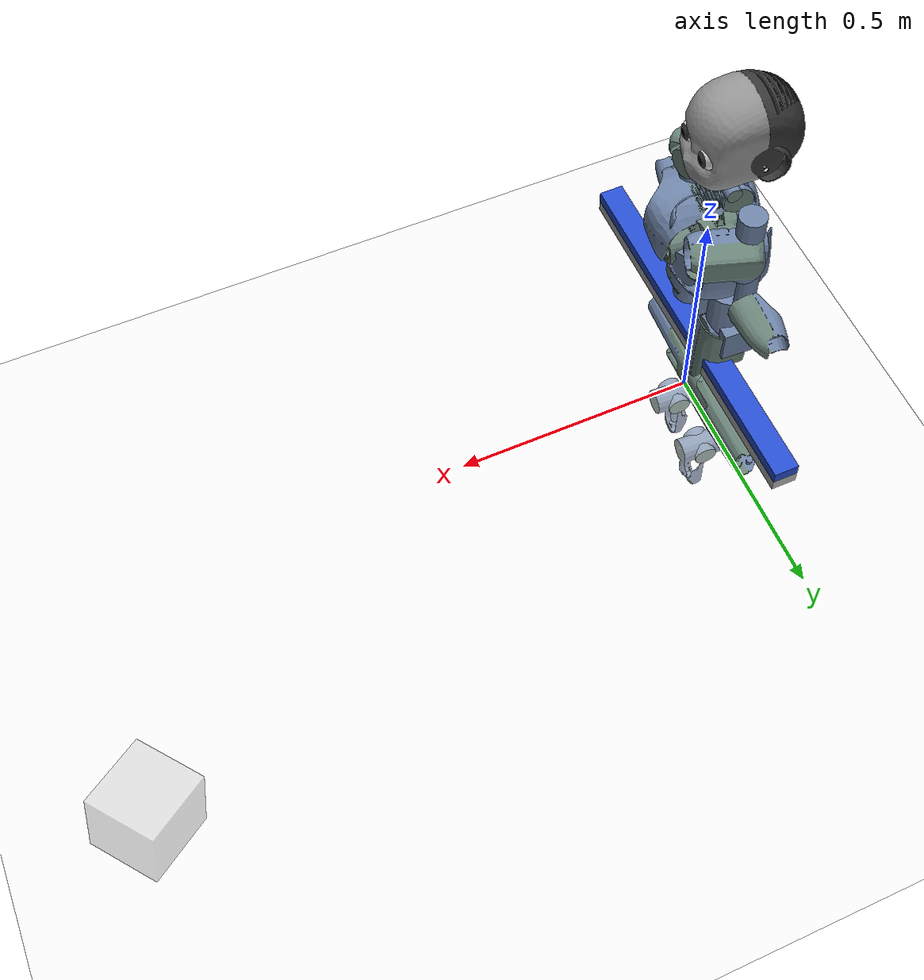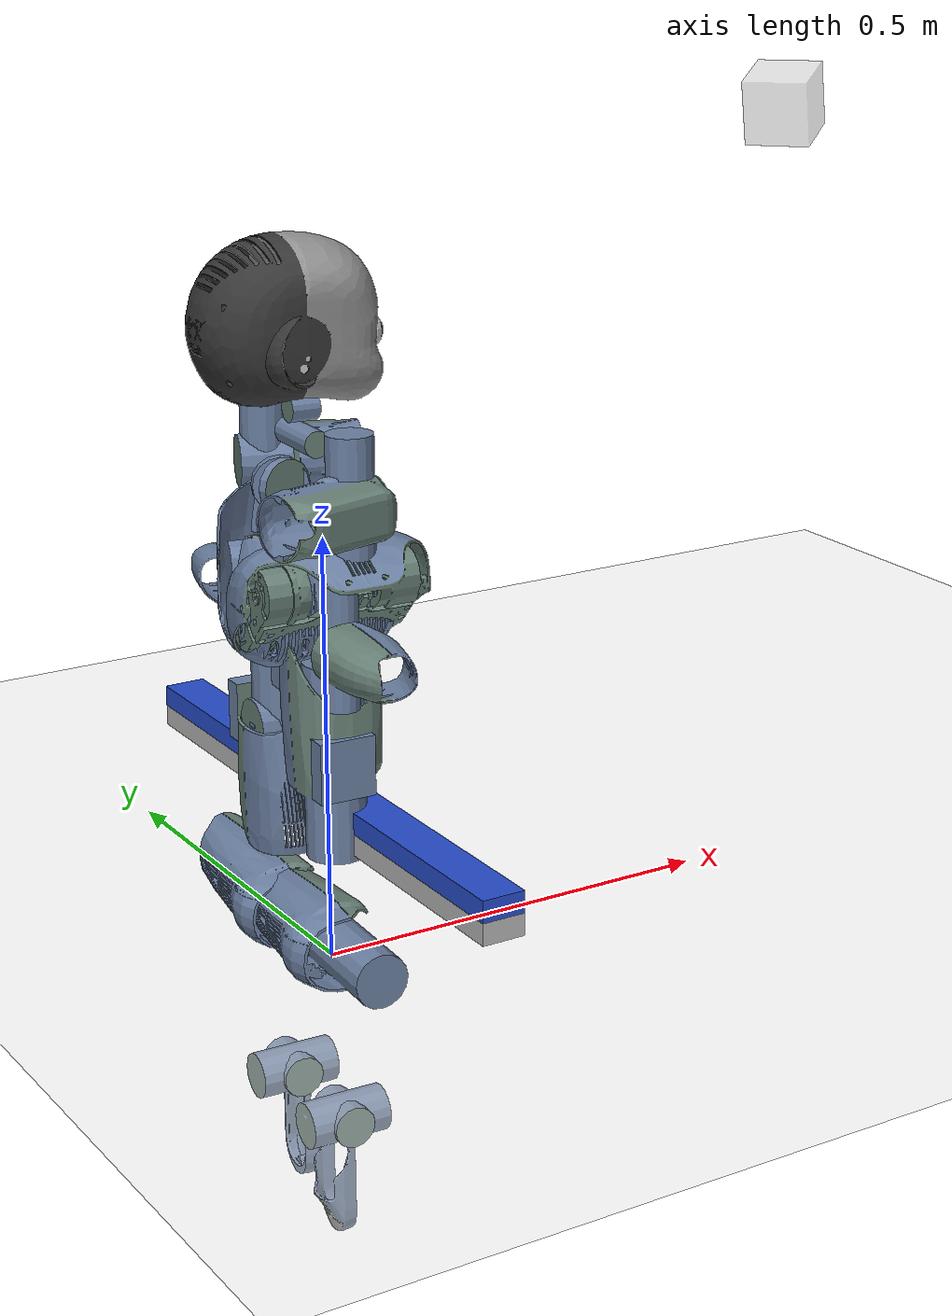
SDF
<sdf version="1.6">
 <world name="default">
  <light name="sun" type="directional">
   <pose>0 0 10 0 -0 0</pose>
   <diffuse>0.8 0.8 0.8 1</diffuse>
   <specular>0.2 0.2 0.2 1</specular>
   <attenuation>
    <range>1000</range>
    <constant>0.9</constant>
    <linear>0.01</linear>
    <quadratic>0.001</quadratic>
   </attenuation>
   <direction>-0.5 0.1 -0.9</direction>
  </light>
  <model name="ground_plane">
   <static>1</static>
   <link name="link">
    <collision name="collision">
     <geometry><plane><normal>0 0 1</normal><size>100 100</size></plane></geometry>
     <surface><friction><ode><mu>100</mu><mu2>50</mu2></ode></friction></surface>
    </collision>
    <visual name="visual">
     <cast_shadows>0</cast_shadows>
     <geometry><plane><normal>0 0 1</normal><size>100 100</size></plane></geometry>
     <material>
      <script><uri>file://media/materials/scripts/gazebo.material</uri><name>Gazebo/White</name></script>
     </material>
    </visual>
   </link>
  </model>
  <physics name="default_physics" default="0" type="ode">
   <max_step_size>0.001</max_step_size>
   <real_time_factor>1</real_time_factor>
   <real_time_update_rate>1000</real_time_update_rate>
  </physics>
  <scene><ambient>1 1 1 1</ambient><background>1 1 1 1</background><shadows>1</shadows></scene>
  <spherical_coordinates>
   <surface_model>EARTH_WGS84</surface_model>
   <latitude_deg>0</latitude_deg>
   <longitude_deg>0</longitude_deg>
   <elevation>0</elevation>
   <heading_deg>0</heading_deg>
  </spherical_coordinates>
  <model name="chair">
   <pose>0 0 1e-06 0 -0 0</pose>
   <link name="chair::low_part">
    <pose>0 0 0.18 0 -0 0</pose>
    <inertial>
     <mass>1</mass>
     <inertia><ixx>1</ixx><ixy>0</ixy><ixz>0</ixz><iyy>1</iyy><iyz>0</iyz><izz>1</izz></inertia>
    </inertial>
    <collision name="collision_low"><geometry><box><size>0.05 0.75 0.025</size></box></geometry></collision>
    <visual name="visual_low"><geometry><box><size>0.05 0.75 0.025</size></box></geometry></visual>
   </link>
   <link name="chair::high_part">
    <pose>0 0 0.205 0 -0 0</pose>
    <inertial>
     <mass>1</mass>
     <inertia><ixx>1</ixx><ixy>0</ixy><ixz>0</ixz><iyy>1</iyy><iyz>0</iyz><izz>1</izz></inertia>
    </inertial>
    <collision name="collision_high">
     <geometry><box><size>0.05 0.75 0.025</size></box></geometry>
     <max_contacts>4</max_contacts>
     <surface>
      <contact>
       <ode>
        <soft_erp>0.2</soft_erp>
        <soft_cfm>0</soft_cfm>
        <kp>1.8e+06</kp>
        <kd>100</kd>
        <max_vel>100</max_vel>
        <min_depth>0.0001</min_depth>
       </ode>
      </contact>
      <friction><ode><mu>1</mu><mu2>1</mu2><fdir1>0 0 0</fdir1><slip1>0</slip1><slip2>0</slip2></ode></friction>
      <bounce><restitution_coefficient>0</restitution_coefficient><threshold>100000</threshold></bounce>
     </surface>
    </collision>
    <visual name="visual_high">
     <material><script><name>Gazebo/Blue</name><uri>__default__</uri></script></material>
     <geometry><box><size>0.05 0.75 0.025</size></box></geometry>
    </visual>
   </link>
   <joint name="chair::sensor_joint" type="fixed">
    <parent>chair::low_part</parent>
    <child>chair::high_part</child>
    <axis>
     <limit><lower>0</lower><upper>0</upper></limit>
     <xyz>0 0 0</xyz>
     <use_parent_model_frame>0</use_parent_model_frame>
    </axis>
    <sensor name="chair_ft_sensor" type="force_torque">
     <force_torque><frame>child</frame><measure_direction>parent_to_child</measure_direction></force_torque>
     <always_on>1</always_on>
     <visualize>1</visualize>
     <update_rate>100</update_rate>
     <plugin name="chair_FT_plugin" filename="libgazebo_yarp_forcetorque.so">
      <yarpConfigurationFile>model://icub_chair_world/chair/chair_gazebo_torque.ini</yarpConfigurationFile>
     </plugin>
    </sensor>
   </joint>
   <joint name="chair::fixed to ground" type="fixed">
    <parent>world</parent>
    <child>chair::low_part</child>
    <axis>
     <limit><lower>0</lower><upper>0</upper></limit>
     <xyz>0 0 0.18</xyz>
     <use_parent_model_frame>0</use_parent_model_frame>
    </axis>
   </joint>
  </model>
  <model name="iCub">
   <pose>-0.025572 -0.00329 0.391415 0.001931 0.002444 3.09517</pose>
   <self_collide>1</self_collide>
   <link name="iCub::root_link">
    <inertial>
     <mass>4.72</mass>
     <inertia><ixx>0.01</ixx><ixy>0</ixy><ixz>0</ixz><iyy>0.01</iyy><iyz>0</iyz><izz>0.01</izz></inertia>
    </inertial>
    <collision name="root_link_collision">
     <geometry>
      <mesh><scale>1 1 1</scale><uri>model://icub/meshes/collision/icub_simple_collision_root_link.dae</uri></mesh>
     </geometry>
    </collision>
    <visual name="root_link_visual">
     <geometry><mesh><scale>1 1 1</scale><uri>model://icub/meshes/visual/icub_root_link.dae</uri></mesh></geometry>
    </visual>
   </link>
   <link name="iCub::l_hip_1">
    <pose>0 -0.0681 -0.1199 3e-06 1.57079 3.14159</pose>
    <inertial>
     <pose>0 -0.0782 0 0 -0 0</pose>
     <mass>0.754</mass>
     <inertia>
      <ixx>0.01</ixx>
      <ixy>2.059e-06</ixy>
      <ixz>1.451e-06</ixz>
      <iyy>0.01</iyy>
      <iyz>1.545e-06</iyz>
      <izz>0.01</izz>
     </inertia>
    </inertial>
    <collision name="l_hip_1_collision">
     <pose>0 0 0 -0.785403 1.57079 -2.35619</pose>
     <geometry>
      <mesh><scale>1 1 1</scale><uri>model://icub/meshes/collision/icub_simple_collision_l_hip_1.dae</uri></mesh>
     </geometry>
    </collision>
    <visual name="l_hip_1_visual">
     <pose>0 0 0 -0.785403 1.57079 -2.35619</pose>
     <geometry><mesh><scale>1 1 1</scale><uri>model://icub/meshes/visual/icub_l_hip_1.dae</uri></mesh></geometry>
    </visual>
   </link>
   <joint name="iCub::l_hip_pitch" type="revolute">
    <child>iCub::l_hip_1</child>
    <parent>iCub::root_link</parent>
    <axis>
     <xyz>3e-06 1 0</xyz>
     <limit><lower>-0.767945</lower><upper>2.30383</upper><effort>84</effort><velocity>100</velocity></limit>
     <dynamics>
      <damping>1</damping>
      <friction>0</friction>
      <spring_reference>0</spring_reference>
      <spring_stiffness>0</spring_stiffness>
     </dynamics>
     <use_parent_model_frame>1</use_parent_model_frame>
    </axis>
   </joint>
   <link name="iCub::l_hip_2">
    <pose>0 -0.0681 -0.1199 3.14159 -7e-06 3.14159</pose>
    <inertial>
     <pose>0 0 0.03045 0 -0 0</pose>
     <mass>0.526</mass>
     <inertia>
      <ixx>0.01</ixx>
      <ixy>-7.4e-08</ixy>
      <ixz>1.0835e-05</ixz>
      <iyy>0.01</iyy>
      <iyz>-6.2e-08</iyz>
      <izz>0.01</izz>
     </inertia>
    </inertial>
    <collision name="l_hip_2_collision">
     <pose>0 0 0 0.785363 -1.57079 2.35623</pose>
     <geometry>
      <mesh><scale>1 1 1</scale><uri>model://icub/meshes/collision/icub_simple_collision_l_hip_2.dae</uri></mesh>
     </geometry>
    </collision>
    <visual name="l_hip_2_visual">
     <pose>0 0 0 0.785363 -1.57079 2.35623</pose>
     <geometry><mesh><scale>1 1 1</scale><uri>model://icub/meshes/visual/icub_l_hip_2.dae</uri></mesh></geometry>
    </visual>
   </link>
   <joint name="iCub::l_hip_roll" type="revolute">
    <child>iCub::l_hip_2</child>
    <parent>iCub::l_hip_1</parent>
    <axis>
     <xyz>-1 3e-06 7e-06</xyz>
     <limit><lower>-0.296706</lower><upper>2.07694</upper><effort>84</effort><velocity>100</velocity></limit>
     <dynamics>
      <damping>1</damping>
      <friction>0</friction>
      <spring_reference>0</spring_reference>
      <spring_stiffness>0</spring_stiffness>
     </dynamics>
     <use_parent_model_frame>1</use_parent_model_frame>
    </axis>
   </joint>
   <link name="iCub::l_hip_3">
    <pose>-0 -0.0681 -0.1864 3.14159 -7e-06 3.14159</pose>
    <inertial>
     <mass>0.1</mass>
     <inertia><ixx>0.01</ixx><ixy>0</ixy><ixz>0</ixz><iyy>0.01</iyy><iyz>0</iyz><izz>0.01</izz></inertia>
    </inertial>
   </link>
   <joint name="iCub::l_leg_ft_sensor" type="revolute">
    <child>iCub::l_hip_3</child>
    <parent>iCub::l_hip_2</parent>
    <axis>
     <xyz>0 0 0</xyz>
     <limit><lower>0</lower><upper>0</upper><effort>0</effort><velocity>0</velocity></limit>
     <dynamics><spring_reference>0</spring_reference><spring_stiffness>0</spring_stiffness></dynamics>
     <use_parent_model_frame>1</use_parent_model_frame>
    </axis>
    <sensor name="left_leg_ft" type="force_torque">
     <always_on>1</always_on>
     <update_rate>100</update_rate>
     <plugin name="left_leg_ft_plugin" filename="libgazebo_yarp_forcetorque.so">
      <yarpConfigurationFile>model://icub/conf/FT/gazebo_icub_left_leg_ft.ini</yarpConfigurationFile>
     </plugin>
    </sensor>
   </joint>
   <link name="iCub::l_upper_leg">
    <pose>0 -0.0681 -0.1199 1.57079 -7e-06 3.14159</pose>
    <inertial>
     <pose>0.00144 -0.15943 -0.00039 0 -0 0</pose>
     <mass>2.175</mass>
     <inertia>
      <ixx>0.01</ixx>
      <ixy>-6.726e-05</ixy>
      <ixz>2.267e-06</ixz>
      <iyy>0.01</iyy>
      <iyz>3.63726e-05</iyz>
      <izz>0.01</izz>
     </inertia>
    </inertial>
    <collision name="l_upper_leg_collision">
     <pose>0 0 0 -2.67797 1.57079 -1.10716</pose>
     <geometry>
      <mesh><scale>1 1 1</scale><uri>model://icub/meshes/collision/icub_simple_collision_l_thigh.dae</uri></mesh>
     </geometry>
     <max_contacts>4</max_contacts>
     <surface>
      <contact>
       <ode>
        <soft_erp>0.2</soft_erp>
        <soft_cfm>0</soft_cfm>
        <kp>1.8e+07</kp>
        <kd>100</kd>
        <max_vel>100</max_vel>
        <min_depth>0.0001</min_depth>
       </ode>
      </contact>
      <friction><ode><mu>1</mu><mu2>1</mu2><fdir1>0 0 0</fdir1><slip1>0</slip1><slip2>0</slip2></ode></friction>
      <bounce><restitution_coefficient>0</restitution_coefficient><threshold>100000</threshold></bounce>
     </surface>
    </collision>
    <visual name="l_upper_leg_visual">
     <pose>0 0 0 -2.67797 1.57079 -1.10716</pose>
     <geometry><mesh><scale>1 1 1</scale><uri>model://icub/meshes/visual/icub_l_thigh.dae</uri></mesh></geometry>
    </visual>
   </link>
   <joint name="iCub::l_hip_yaw" type="revolute">
    <child>iCub::l_upper_leg</child>
    <parent>iCub::l_hip_3</parent>
    <axis>
     <xyz>7e-06 -6e-06 1</xyz>
     <limit><lower>-1.37881</lower><upper>1.37881</upper><effort>40</effort><velocity>100</velocity></limit>
     <dynamics>
      <damping>1</damping>
      <friction>0</friction>
      <spring_reference>0</spring_reference>
      <spring_stiffness>0</spring_stiffness>
     </dynamics>
     <use_parent_model_frame>1</use_parent_model_frame>
    </axis>
   </joint>
   <link name="iCub::l_lower_leg">
    <pose>-2e-06 -0.068099 -0.3435 2.09198 -1.57078 -0.521189</pose>
    <inertial>
     <pose>-0.1071 0.00182 0.00211 0 -0 0</pose>
     <mass>1.264</mass>
     <inertia>
      <ixx>0.01</ixx>
      <ixy>-0.000185699</ixy>
      <ixz>-6.3147e-05</ixz>
      <iyy>0.01</iyy>
      <iyz>7.86e-07</iyz>
      <izz>0.01</izz>
     </inertia>
    </inertial>
    <collision name="l_lower_leg_collision">
     <pose>0 0 0 -3.14159 -0 1.5708</pose>
     <geometry>
      <mesh><scale>1 1 1</scale><uri>model://icub/meshes/collision/icub_simple_collision_l_shank.dae</uri></mesh>
     </geometry>
    </collision>
    <visual name="l_lower_leg_visual">
     <pose>0 0 0 -3.14159 -0 1.5708</pose>
     <geometry><mesh><scale>1 1 1</scale><uri>model://icub/meshes/visual/icub_l_shank.dae</uri></mesh></geometry>
    </visual>
   </link>
   <joint name="iCub::l_knee" type="revolute">
    <child>iCub::l_lower_leg</child>
    <parent>iCub::l_upper_leg</parent>
    <axis>
     <xyz>5e-06 1 6e-06</xyz>
     <limit><lower>-2.18166</lower><upper>0.401426</upper><effort>30</effort><velocity>100</velocity></limit>
     <dynamics>
      <damping>1</damping>
      <friction>0</friction>
      <spring_reference>0</spring_reference>
      <spring_stiffness>0</spring_stiffness>
     </dynamics>
     <use_parent_model_frame>1</use_parent_model_frame>
    </axis>
   </joint>
   <link name="iCub::l_ankle_1">
    <pose>-4e-06 -0.068097 -0.5565 0.52118 -1.57078 -0.521189</pose>
    <inertial>
     <pose>-0.0054 0.00163 0.0172 0 -0 0</pose>
     <mass>0.746</mass>
     <inertia>
      <ixx>0.01</ixx>
      <ixy>-7.081e-06</ixy>
      <ixz>4.1421e-05</ixz>
      <iyy>0.01</iyy>
      <iyz>2.0817e-05</iyz>
      <izz>0.01</izz>
     </inertia>
    </inertial>
    <collision name="l_ankle_1_collision">
     <pose>0 -0 0 1.5708 -0 0</pose>
     <geometry>
      <mesh><scale>1 1 1</scale><uri>model://icub/meshes/collision/icub_simple_collision_l_ankle_1.dae</uri></mesh>
     </geometry>
    </collision>
    <visual name="l_ankle_1_visual">
     <pose>0 -0 0 1.5708 -0 0</pose>
     <geometry><mesh><scale>1 1 1</scale><uri>model://icub/meshes/visual/icub_l_ankle_1.dae</uri></mesh></geometry>
    </visual>
   </link>
   <joint name="iCub::l_ankle_pitch" type="revolute">
    <child>iCub::l_ankle_1</child>
    <parent>iCub::l_lower_leg</parent>
    <axis>
     <xyz>-9e-06 -1 -6e-06</xyz>
     <limit><lower>-0.733038</lower><upper>0.366519</upper><effort>24</effort><velocity>100</velocity></limit>
     <dynamics>
      <damping>1</damping>
      <friction>0</friction>
      <spring_reference>0</spring_reference>
      <spring_stiffness>0</spring_stiffness>
     </dynamics>
     <use_parent_model_frame>1</use_parent_model_frame>
    </axis>
   </joint>
   <link name="iCub::l_ankle_2">
    <pose>-4e-06 -0.068097 -0.5565 3.14159 -7e-06 3.14158</pose>
    <inertial>
     <pose>0 0 0.037 0 -0 0</pose>
     <mass>0.2675</mass>
     <inertia><ixx>0.01</ixx><ixy>0</ixy><ixz>0</ixz><iyy>0.01</iyy><iyz>0</iyz><izz>0.01</izz></inertia>
    </inertial>
   </link>
   <joint name="iCub::l_ankle_roll" type="revolute">
    <child>iCub::l_ankle_2</child>
    <parent>iCub::l_ankle_1</parent>
    <axis>
     <xyz>-1 9e-06 7e-06</xyz>
     <limit><lower>-0.418879</lower><upper>0.418879</upper><effort>11</effort><velocity>100</velocity></limit>
     <dynamics>
      <damping>1</damping>
      <friction>0</friction>
      <spring_reference>0</spring_reference>
      <spring_stiffness>0</spring_stiffness>
     </dynamics>
     <use_parent_model_frame>1</use_parent_model_frame>
    </axis>
   </joint>
   <link name="iCub::l_foot">
    <pose>-4e-06 -0.068097 -0.5935 3.14159 -7e-06 3.14158</pose>
    <inertial>
     <pose>0.024069 -0.000614 -0.028415 0 -0 0</pose>
     <mass>0.5935</mass>
     <inertia>
      <ixx>0.01</ixx>
      <ixy>-4.51893e-06</ixy>
      <ixz>0.000567785</ixz>
      <iyy>0.01</iyy>
      <iyz>-6.62361e-07</iyz>
      <izz>0.01</izz>
     </inertia>
    </inertial>
    <collision name="l_foot_collision">
     <pose>0.03 0 -0.01 0 -0 0</pose>
     <geometry><box><size>0.15 0.07 0.03</size></box></geometry>
     <max_contacts>4</max_contacts>
     <surface>
      <contact>
       <ode>
        <soft_erp>0.2</soft_erp>
        <soft_cfm>0</soft_cfm>
        <kp>1.8e+07</kp>
        <kd>100</kd>
        <max_vel>100</max_vel>
        <min_depth>0.0001</min_depth>
       </ode>
      </contact>
      <friction><ode><mu>1</mu><mu2>1</mu2><fdir1>0 0 0</fdir1><slip1>0</slip1><slip2>0</slip2></ode></friction>
      <bounce><restitution_coefficient>0</restitution_coefficient><threshold>100000</threshold></bounce>
     </surface>
    </collision>
    <visual name="l_foot_visual">
     <pose>0 -0 -0.037 -0.785403 1.57079 -0.785403</pose>
     <geometry><mesh><scale>1 1 1</scale><uri>model://icub/meshes/visual/icub_l_foot.dae</uri></mesh></geometry>
    </visual>
   </link>
   <joint name="iCub::l_foot_ft_sensor" type="revolute">
    <child>iCub::l_foot</child>
    <parent>iCub::l_ankle_2</parent>
    <axis>
     <xyz>0 0 0</xyz>
     <limit><lower>0</lower><upper>0</upper><effort>0</effort><velocity>0</velocity></limit>
     <dynamics><spring_reference>0</spring_reference><spring_stiffness>0</spring_stiffness></dynamics>
     <use_parent_model_frame>1</use_parent_model_frame>
    </axis>
    <sensor name="left_foot_ft" type="force_torque">
     <always_on>1</always_on>
     <update_rate>100</update_rate>
     <plugin name="left_foot_ft_plugin" filename="libgazebo_yarp_forcetorque.so">
      <yarpConfigurationFile>model://icub/conf/FT/gazebo_icub_left_foot_ft.ini</yarpConfigurationFile>
     </plugin>
    </sensor>
   </joint>
   <link name="iCub::r_hip_1">
    <pose>0 0.0681 -0.1199 3.14159 1.57079 -3.14159</pose>
    <inertial>
     <pose>0 -0.0782 0 0 -0 0</pose>
     <mass>0.754</mass>
     <inertia><ixx>0.01</ixx><ixy>0</ixy><ixz>0</ixz><iyy>0.01</iyy><iyz>0</iyz><izz>0.01</izz></inertia>
    </inertial>
    <collision name="r_hip_1_collision">
     <pose>0 0 0 1.76819 -1.57079 2.76109</pose>
     <geometry>
      <mesh><scale>1 1 1</scale><uri>model://icub/meshes/collision/icub_simple_collision_r_hip_1.dae</uri></mesh>
     </geometry>
    </collision>
    <visual name="r_hip_1_visual">
     <pose>0 0 0 1.76819 -1.57079 2.76109</pose>
     <geometry><mesh><scale>1 1 1</scale><uri>model://icub/meshes/visual/icub_r_hip_1.dae</uri></mesh></geometry>
    </visual>
   </link>
   <joint name="iCub::r_hip_pitch" type="revolute">
    <child>iCub::r_hip_1</child>
    <parent>iCub::root_link</parent>
    <axis>
     <xyz>0 1 0</xyz>
     <limit><lower>-0.767945</lower><upper>2.30383</upper><effort>84</effort><velocity>100</velocity></limit>
     <dynamics>
      <damping>1</damping>
      <friction>0</friction>
      <spring_reference>0</spring_reference>
      <spring_stiffness>0</spring_stiffness>
     </dynamics>
     <use_parent_model_frame>1</use_parent_model_frame>
    </axis>
   </joint>
   <link name="iCub::r_hip_2">
    <pose>0 0.0681 -0.1199 -3.14159 -7e-06 -3.14159</pose>
    <inertial>
     <pose>0 0 0.03045 0 -0 0</pose>
     <mass>0.526</mass>
     <inertia><ixx>0.01</ixx><ixy>0</ixy><ixz>0</ixz><iyy>0.01</iyy><iyz>0</iyz><izz>0.01</izz></inertia>
    </inertial>
    <collision name="r_hip_2_collision">
     <pose>0 0 0 -2.35627 -1.57079 2.35627</pose>
     <geometry>
      <mesh><scale>1 1 1</scale><uri>model://icub/meshes/collision/icub_simple_collision_r_hip_2.dae</uri></mesh>
     </geometry>
    </collision>
    <visual name="r_hip_2_visual">
     <pose>0 0 0 -2.35627 -1.57079 2.35627</pose>
     <geometry><mesh><scale>1 1 1</scale><uri>model://icub/meshes/visual/icub_r_hip_2.dae</uri></mesh></geometry>
    </visual>
   </link>
   <joint name="iCub::r_hip_roll" type="revolute">
    <child>iCub::r_hip_2</child>
    <parent>iCub::r_hip_1</parent>
    <axis>
     <xyz>1 0 -7e-06</xyz>
     <limit><lower>-0.296706</lower><upper>2.07694</upper><effort>84</effort><velocity>100</velocity></limit>
     <dynamics>
      <damping>1</damping>
      <friction>0</friction>
      <spring_reference>0</spring_reference>
      <spring_stiffness>0</spring_stiffness>
     </dynamics>
     <use_parent_model_frame>1</use_parent_model_frame>
    </axis>
   </joint>
   <link name="iCub::r_hip_3">
    <pose>-0 0.0681 -0.1864 -3.14159 -7e-06 -3.14159</pose>
    <inertial>
     <mass>0.1</mass>
     <inertia><ixx>0.01</ixx><ixy>0</ixy><ixz>0</ixz><iyy>0.01</iyy><iyz>0</iyz><izz>0.01</izz></inertia>
    </inertial>
   </link>
   <joint name="iCub::r_leg_ft_sensor" type="revolute">
    <child>iCub::r_hip_3</child>
    <parent>iCub::r_hip_2</parent>
    <axis>
     <xyz>0 0 0</xyz>
     <limit><lower>0</lower><upper>0</upper><effort>0</effort><velocity>0</velocity></limit>
     <dynamics><spring_reference>0</spring_reference><spring_stiffness>0</spring_stiffness></dynamics>
     <use_parent_model_frame>1</use_parent_model_frame>
    </axis>
    <sensor name="right_leg_ft" type="force_torque">
     <always_on>1</always_on>
     <update_rate>100</update_rate>
     <plugin name="right_leg_ft_plugin" filename="libgazebo_yarp_forcetorque.so">
      <yarpConfigurationFile>model://icub/conf/FT/gazebo_icub_right_leg_ft.ini</yarpConfigurationFile>
     </plugin>
    </sensor>
   </joint>
   <link name="iCub::r_upper_leg">
    <pose>0 0.0681 -0.1199 1.57079 -7e-06 3.14159</pose>
    <inertial>
     <pose>0.00144 -0.15943 0.00039 0 -0 0</pose>
     <mass>2.175</mass>
     <inertia>
      <ixx>0.01</ixx>
      <ixy>0</ixy>
      <ixz>0</ixz>
      <iyy>0.01</iyy>
      <iyz>-2.71051e-20</iyz>
      <izz>0.01</izz>
     </inertia>
    </inertial>
    <collision name="r_upper_leg_collision">
     <pose>0 0 0 1.57087 -1.57079 -7.3e-05</pose>
     <geometry>
      <mesh><scale>1 1 1</scale><uri>model://icub/meshes/collision/icub_simple_collision_r_thigh.dae</uri></mesh>
     </geometry>
     <max_contacts>4</max_contacts>
     <surface>
      <contact>
       <ode>
        <soft_erp>0.2</soft_erp>
        <soft_cfm>0</soft_cfm>
        <kp>1.8e+07</kp>
        <kd>100</kd>
        <max_vel>100</max_vel>
        <min_depth>0.0001</min_depth>
       </ode>
      </contact>
      <friction><ode><mu>1</mu><mu2>1</mu2><fdir1>0 0 0</fdir1><slip1>0</slip1><slip2>0</slip2></ode></friction>
      <bounce><restitution_coefficient>0</restitution_coefficient><threshold>100000</threshold></bounce>
     </surface>
    </collision>
    <visual name="r_upper_leg_visual">
     <pose>0 0 0 1.57087 -1.57079 -7.3e-05</pose>
     <geometry><mesh><scale>1 1 1</scale><uri>model://icub/meshes/visual/icub_r_thigh.dae</uri></mesh></geometry>
    </visual>
   </link>
   <joint name="iCub::r_hip_yaw" type="revolute">
    <child>iCub::r_upper_leg</child>
    <parent>iCub::r_hip_3</parent>
    <axis>
     <xyz>-7e-06 4e-06 -1</xyz>
     <limit><lower>-1.37881</lower><upper>1.37881</upper><effort>40</effort><velocity>100</velocity></limit>
     <dynamics>
      <damping>1</damping>
      <friction>0</friction>
      <spring_reference>0</spring_reference>
      <spring_stiffness>0</spring_stiffness>
     </dynamics>
     <use_parent_model_frame>1</use_parent_model_frame>
    </axis>
   </joint>
   <link name="iCub::r_lower_leg">
    <pose>-2e-06 0.068101 -0.3435 1.89254 -1.57078 -0.321751</pose>
    <inertial>
     <pose>-0.1071 0.00182 -0.00211 0 -0 0</pose>
     <mass>1.264</mass>
     <inertia>
      <ixx>0.01</ixx>
      <ixy>5.42101e-20</ixy>
      <ixz>-5.42101e-20</ixz>
      <iyy>0.01</iyy>
      <iyz>8.47033e-22</iyz>
      <izz>0.01</izz>
     </inertia>
    </inertial>
    <collision name="r_lower_leg_collision">
     <pose>0 0 -0 3.14159 -0 1.5708</pose>
     <geometry>
      <mesh><scale>1 1 1</scale><uri>model://icub/meshes/collision/icub_simple_collision_r_shank.dae</uri></mesh>
     </geometry>
    </collision>
    <visual name="r_lower_leg_visual">
     <pose>0 0 -0 3.14159 -0 1.5708</pose>
     <geometry><mesh><scale>1 1 1</scale><uri>model://icub/meshes/visual/icub_r_shank.dae</uri></mesh></geometry>
    </visual>
   </link>
   <joint name="iCub::r_knee" type="revolute">
    <child>iCub::r_lower_leg</child>
    <parent>iCub::r_upper_leg</parent>
    <axis>
     <xyz>3e-06 1 4e-06</xyz>
     <limit><lower>-2.18166</lower><upper>0.401426</upper><effort>30</effort><velocity>100</velocity></limit>
     <dynamics>
      <damping>1</damping>
      <friction>0</friction>
      <spring_reference>0</spring_reference>
      <spring_stiffness>0</spring_stiffness>
     </dynamics>
     <use_parent_model_frame>1</use_parent_model_frame>
    </axis>
   </joint>
   <link name="iCub::r_ankle_1">
    <pose>-4e-06 0.068102 -0.5565 -2.81984 -1.57078 -0.321751</pose>
    <inertial>
     <pose>-0.0054 0.00163 -0.0172 0 -0 0</pose>
     <mass>0.746</mass>
     <inertia>
      <ixx>0.01</ixx>
      <ixy>-1.69407e-21</ixy>
      <ixz>1.35525e-20</ixz>
      <iyy>0.01</iyy>
      <iyz>3.38813e-21</iyz>
      <izz>0.01</izz>
     </inertia>
    </inertial>
    <collision name="r_ankle_1_collision">
     <pose>0 -0 -0 -1.5708 -0 0</pose>
     <geometry>
      <mesh><scale>1 1 1</scale><uri>model://icub/meshes/collision/icub_simple_collision_r_ankle_1.dae</uri></mesh>
     </geometry>
    </collision>
    <visual name="r_ankle_1_visual">
     <pose>0 -0 -0 -1.5708 -0 0</pose>
     <geometry><mesh><scale>1 1 1</scale><uri>model://icub/meshes/visual/icub_r_ankle_1.dae</uri></mesh></geometry>
    </visual>
   </link>
   <joint name="iCub::r_ankle_pitch" type="revolute">
    <child>iCub::r_ankle_1</child>
    <parent>iCub::r_lower_leg</parent>
    <axis>
     <xyz>1e-06 -1 -4e-06</xyz>
     <limit><lower>-0.733038</lower><upper>0.366519</upper><effort>24</effort><velocity>100</velocity></limit>
     <dynamics>
      <damping>1</damping>
      <friction>0</friction>
      <spring_reference>0</spring_reference>
      <spring_stiffness>0</spring_stiffness>
     </dynamics>
     <use_parent_model_frame>1</use_parent_model_frame>
    </axis>
   </joint>
   <link name="iCub::r_ankle_2">
    <pose>-4e-06 0.068102 -0.5565 3.14159 -1.4e-05 -3.14159</pose>
    <inertial>
     <pose>0 0 0.037 0 -0 0</pose>
     <mass>0.2675</mass>
     <inertia><ixx>0.01</ixx><ixy>0</ixy><ixz>0</ixz><iyy>0.01</iyy><iyz>0</iyz><izz>0.01</izz></inertia>
    </inertial>
   </link>
   <joint name="iCub::r_ankle_roll" type="revolute">
    <child>iCub::r_ankle_2</child>
    <parent>iCub::r_ankle_1</parent>
    <axis>
     <xyz>1 3e-06 -1.4e-05</xyz>
     <limit><lower>-0.418879</lower><upper>0.418879</upper><effort>11</effort><velocity>100</velocity></limit>
     <dynamics>
      <damping>1</damping>
      <friction>0</friction>
      <spring_reference>0</spring_reference>
      <spring_stiffness>0</spring_stiffness>
     </dynamics>
     <use_parent_model_frame>1</use_parent_model_frame>
    </axis>
   </joint>
   <link name="iCub::r_foot">
    <pose>-5e-06 0.068102 -0.5935 3.14159 -1.4e-05 -3.14159</pose>
    <inertial>
     <pose>0.024069 0.000614 -0.028415 0 -0 0</pose>
     <mass>0.5935</mass>
     <inertia>
      <ixx>0.01</ixx>
      <ixy>4.51893e-06</ixy>
      <ixz>0.000567784</ixz>
      <iyy>0.01</iyy>
      <iyz>6.62535e-07</iyz>
      <izz>0.01</izz>
     </inertia>
    </inertial>
    <collision name="r_foot_collision">
     <pose>0.03 0 -0.01 0 -0 0</pose>
     <geometry><box><size>0.15 0.07 0.03</size></box></geometry>
     <max_contacts>4</max_contacts>
     <surface>
      <contact>
       <ode>
        <soft_erp>0.2</soft_erp>
        <soft_cfm>0</soft_cfm>
        <kp>1.8e+07</kp>
        <kd>100</kd>
        <max_vel>100</max_vel>
        <min_depth>0.0001</min_depth>
       </ode>
      </contact>
      <friction><ode><mu>1</mu><mu2>1</mu2><fdir1>0 0 0</fdir1><slip1>0</slip1><slip2>0</slip2></ode></friction>
      <bounce><restitution_coefficient>0</restitution_coefficient><threshold>100000</threshold></bounce>
     </surface>
    </collision>
    <visual name="r_foot_visual">
     <pose>0 0 -0.037 -2.81983 1.57079 0.321763</pose>
     <geometry><mesh><scale>1 1 1</scale><uri>model://icub/meshes/visual/icub_r_foot.dae</uri></mesh></geometry>
    </visual>
   </link>
   <joint name="iCub::r_foot_ft_sensor" type="revolute">
    <child>iCub::r_foot</child>
    <parent>iCub::r_ankle_2</parent>
    <axis>
     <xyz>0 0 0</xyz>
     <limit><lower>0</lower><upper>0</upper><effort>0</effort><velocity>0</velocity></limit>
     <dynamics><spring_reference>0</spring_reference><spring_stiffness>0</spring_stiffness></dynamics>
     <use_parent_model_frame>1</use_parent_model_frame>
    </axis>
    <sensor name="right_foot_ft" type="force_torque">
     <always_on>1</always_on>
     <update_rate>100</update_rate>
     <plugin name="right_foot_ft_plugin" filename="libgazebo_yarp_forcetorque.so">
      <yarpConfigurationFile>model://icub/conf/FT/gazebo_icub_right_foot_ft.ini</yarpConfigurationFile>
     </plugin>
    </sensor>
   </joint>
   <link name="iCub::torso_1">
    <pose>0 0 0 3.14159 -1.57079 -3e-06</pose>
    <inertial>
     <mass>0.1</mass>
     <inertia>
      <ixx>0.01</ixx>
      <ixy>-4.263e-05</ixy>
      <ixz>-3.889e-08</ixz>
      <iyy>0.01</iyy>
      <iyz>0</iyz>
      <izz>0.01</izz>
     </inertia>
    </inertial>
    <collision name="torso_1_collision">
     <pose>0 0 0 -1.5708 0 0</pose>
     <geometry>
      <mesh><scale>1 1 1</scale><uri>model://icub/meshes/collision/icub_simple_collision_lap_belt_1.dae</uri></mesh>
     </geometry>
    </collision>
    <visual name="torso_1_visual">
     <pose>0 0 0 -1.5708 0 0</pose>
     <geometry>
      <mesh><scale>1 1 1</scale><uri>model://icub/meshes/visual/icub_lap_belt_1.dae</uri></mesh>
     </geometry>
    </visual>
   </link>
   <joint name="iCub::torso_pitch" type="revolute">
    <child>iCub::torso_1</child>
    <parent>iCub::root_link</parent>
    <axis>
     <xyz>-3e-06 -1 0</xyz>
     <limit><lower>-0.383972</lower><upper>1.46608</upper><effort>36</effort><velocity>100</velocity></limit>
     <dynamics>
      <damping>1</damping>
      <friction>0</friction>
      <spring_reference>0</spring_reference>
      <spring_stiffness>0</spring_stiffness>
     </dynamics>
     <use_parent_model_frame>1</use_parent_model_frame>
    </axis>
   </joint>
   <link name="iCub::torso_2">
    <pose>0 -0 0.032 -3.14159 4e-06 1.57079</pose>
    <inertial>
     <mass>0.1</mass>
     <inertia>
      <ixx>0.01</ixx>
      <ixy>-1.923e-06</ixy>
      <ixz>5.095e-05</ixz>
      <iyy>0.01</iyy>
      <iyz>-3.849e-07</iyz>
      <izz>0.01</izz>
     </inertia>
    </inertial>
   </link>
   <joint name="iCub::torso_roll" type="revolute">
    <child>iCub::torso_2</child>
    <parent>iCub::torso_1</parent>
    <axis>
     <xyz>1 -3e-06 -7e-06</xyz>
     <limit><lower>-0.680678</lower><upper>0.680678</upper><effort>80</effort><velocity>100</velocity></limit>
     <dynamics>
      <damping>1</damping>
      <friction>0</friction>
      <spring_reference>0</spring_reference>
      <spring_stiffness>0</spring_stiffness>
     </dynamics>
     <use_parent_model_frame>1</use_parent_model_frame>
    </axis>
   </joint>
   <link name="iCub::chest">
    <pose>-0.0055 0 0.032 1.5708 -7e-06 -3.14159</pose>
    <inertial>
     <pose>0.002229 0.075 -0 0 -0 0</pose>
     <mass>4.81</mass>
     <inertia>
      <ixx>0.07472</ixx>
      <ixy>-3.6e-06</ixy>
      <ixz>-4.705e-05</ixz>
      <iyy>0.08145</iyy>
      <iyz>0.004567</iyz>
      <izz>0.01306</izz>
     </inertia>
    </inertial>
    <collision name="chest_collision">
     <pose>-0.0055 -0 -0 -1.10717 -1.57079 2.67798</pose>
     <geometry>
      <mesh><scale>1 1 1</scale><uri>model://icub/meshes/collision/icub_simple_collision_chest.dae</uri></mesh>
     </geometry>
    </collision>
    <visual name="chest_visual">
     <pose>-0.0055 -0 -0 -1.10717 -1.57079 2.67798</pose>
     <geometry><mesh><scale>1 1 1</scale><uri>model://icub/meshes/visual/icub_chest.dae</uri></mesh></geometry>
    </visual>
   </link>
   <joint name="iCub::torso_yaw" type="revolute">
    <child>iCub::chest</child>
    <parent>iCub::torso_2</parent>
    <axis>
     <xyz>-7e-06 0 -1</xyz>
     <limit><lower>-1.02974</lower><upper>1.02974</upper><effort>80</effort><velocity>100</velocity></limit>
     <dynamics>
      <damping>1</damping>
      <friction>0</friction>
      <spring_reference>0</spring_reference>
      <spring_stiffness>0</spring_stiffness>
     </dynamics>
     <use_parent_model_frame>1</use_parent_model_frame>
    </axis>
   </joint>
   <link name="iCub::l_shoulder_1">
    <pose>-0.010749 -0.11026 0.1753 -0.261794 -1.57079 -1e-06</pose>
    <inertial>
     <pose>-5e-06 0.0187 -0.00119 0 -0 0</pose>
     <mass>0.189</mass>
     <inertia>
      <ixx>0.01</ixx>
      <ixy>9e-09</ixy>
      <ixz>0</ixz>
      <iyy>0.01</iyy>
      <iyz>-1.7e-08</iyz>
      <izz>0.01</izz>
     </inertia>
    </inertial>
    <collision name="l_shoulder_1_collision">
     <pose>0 0.109285 -0.005211 -0.301063 1.57079 -1.87186</pose>
     <geometry>
      <mesh>
       <scale>1 1 1</scale>
       <uri>model://icub/meshes/collision/icub_simple_collision_l_shoulder_1.dae</uri>
      </mesh>
     </geometry>
    </collision>
    <visual name="l_shoulder_1_visual">
     <pose>0 0.109285 -0.005211 -0.301063 1.57079 -1.87186</pose>
     <geometry>
      <mesh><scale>1 1 1</scale><uri>model://icub/meshes/visual/icub_l_shoulder_1.dae</uri></mesh>
     </geometry>
    </visual>
   </link>
   <joint name="iCub::l_shoulder_pitch" type="revolute">
    <child>iCub::l_shoulder_1</child>
    <parent>iCub::chest</parent>
    <axis>
     <xyz>-0.258815 -0.965927 3e-06</xyz>
     <limit><lower>-1.65806</lower><upper>0.0872665</upper><effort>84</effort><velocity>100</velocity></limit>
     <dynamics>
      <damping>1</damping>
      <friction>0</friction>
      <spring_reference>0</spring_reference>
      <spring_stiffness>0</spring_stiffness>
     </dynamics>
     <use_parent_model_frame>1</use_parent_model_frame>
    </axis>
   </joint>
   <link name="iCub::l_shoulder_2">
    <pose>-0.010749 -0.11026 0.1753 3.14159 1e-06 -1.83259</pose>
    <inertial>
     <pose>9.4e-05 -0.00627 0.0166 0 -0 0</pose>
     <mass>0.179</mass>
     <inertia>
      <ixx>0.01</ixx>
      <ixy>4.66e-07</ixy>
      <ixz>3.65e-07</ixz>
      <iyy>0.01</iyy>
      <iyz>-2.0524e-05</iyz>
      <izz>0.01</izz>
     </inertia>
    </inertial>
    <collision name="l_shoulder_2_collision">
     <pose>-0.001545 -0.005211 -0 -2.14033 1.57079 -0.569533</pose>
     <geometry>
      <mesh>
       <scale>1 1 1</scale>
       <uri>model://icub/meshes/collision/icub_simple_collision_l_shoulder_2.dae</uri>
      </mesh>
     </geometry>
    </collision>
    <visual name="l_shoulder_2_visual">
     <pose>-0.001545 -0.005211 -0 -2.14033 1.57079 -0.569533</pose>
     <geometry>
      <mesh><scale>1 1 1</scale><uri>model://icub/meshes/visual/icub_l_shoulder_2.dae</uri></mesh>
     </geometry>
    </visual>
   </link>
   <joint name="iCub::l_shoulder_roll" type="revolute">
    <child>iCub::l_shoulder_2</child>
    <parent>iCub::l_shoulder_1</parent>
    <axis>
     <xyz>-0.965927 0.258815 7e-06</xyz>
     <limit><lower>0</lower><upper>2.80649</upper><effort>84</effort><velocity>100</velocity></limit>
     <dynamics>
      <damping>1</damping>
      <friction>0</friction>
      <spring_reference>0</spring_reference>
      <spring_stiffness>0</spring_stiffness>
     </dynamics>
     <use_parent_model_frame>1</use_parent_model_frame>
    </axis>
   </joint>
   <link name="iCub::l_shoulder_3">
    <pose>-0.010749 -0.11026 0.1753 3.14159 -7e-06 -3.14159</pose>
    <inertial>
     <pose>0.005594 9.8e-05 0.050135 0 -0 0</pose>
     <mass>0.156157</mass>
     <inertia>
      <ixx>0.01</ixx>
      <ixy>-5.662e-08</ixy>
      <ixz>-4.3618e-06</ixz>
      <iyy>0.01</iyy>
      <iyz>-7.42844e-07</iyz>
      <izz>0.01</izz>
     </inertia>
    </inertial>
   </link>
   <joint name="iCub::l_shoulder_yaw" type="revolute">
    <child>iCub::l_shoulder_3</child>
    <parent>iCub::l_shoulder_2</parent>
    <axis>
     <xyz>-7e-06 3e-06 -1</xyz>
     <limit><lower>-0.645772</lower><upper>1.74533</upper><effort>34</effort><velocity>100</velocity></limit>
     <dynamics>
      <damping>1</damping>
      <friction>0</friction>
      <spring_reference>0</spring_reference>
      <spring_stiffness>0</spring_stiffness>
     </dynamics>
     <use_parent_model_frame>1</use_parent_model_frame>
    </axis>
   </joint>
   <link name="iCub::l_upper_arm">
    <pose>-0.025749 -0.11026 0.1073 3.14159 -7e-06 -3.14159</pose>
    <inertial>
     <pose>-0.000156 -9.9e-05 0.0298 0 -0 0</pose>
     <mass>0.727843</mass>
     <inertia>
      <ixx>0.01</ixx>
      <ixy>-1.08e-06</ixy>
      <ixz>-2.29e-06</ixz>
      <iyy>0.01</iyy>
      <iyz>3.57e-06</iyz>
      <izz>0.01</izz>
     </inertia>
    </inertial>
    <collision name="l_upper_arm_collision">
     <pose>-0.020433 0.000144 -0.068 0 0 -1.309</pose>
     <geometry>
      <mesh><scale>1 1 1</scale><uri>model://icub/meshes/collision/icub_simple_collision_l_arm.dae</uri></mesh>
     </geometry>
    </collision>
    <visual name="l_upper_arm_visual">
     <pose>-0.020433 0.000144 -0.068 0 0 -1.309</pose>
     <geometry><mesh><scale>1 1 1</scale><uri>model://icub/meshes/visual/icub_l_arm.dae</uri></mesh></geometry>
    </visual>
   </link>
   <joint name="iCub::l_arm_ft_sensor" type="revolute">
    <child>iCub::l_upper_arm</child>
    <parent>iCub::l_shoulder_3</parent>
    <axis>
     <xyz>0 0 0</xyz>
     <limit><lower>0</lower><upper>0</upper><effort>0</effort><velocity>0</velocity></limit>
     <dynamics><spring_reference>0</spring_reference><spring_stiffness>0</spring_stiffness></dynamics>
     <use_parent_model_frame>1</use_parent_model_frame>
    </axis>
    <sensor name="left_arm_ft" type="force_torque">
     <always_on>1</always_on>
     <update_rate>100</update_rate>
     <plugin name="left_arm_ft_plugin" filename="libgazebo_yarp_forcetorque.so">
      <yarpConfigurationFile>model://icub/conf/FT/gazebo_icub_left_arm_ft.ini</yarpConfigurationFile>
     </plugin>
    </sensor>
   </joint>
   <link name="iCub::l_elbow_1">
    <pose>-0.02575 -0.11026 0.02302 3.14159 -7e-06 -3.14159</pose>
    <inertial>
     <pose>-0.0013 0.00371 -0.00105 0 -0 0</pose>
     <mass>0.1</mass>
     <inertia>
      <ixx>0.01</ixx>
      <ixy>-5.15e-07</ixy>
      <ixz>-4.08e-07</ixz>
      <iyy>0.01</iyy>
      <iyz>-3.71e-07</iyz>
      <izz>0.01</izz>
     </inertia>
    </inertial>
   </link>
   <joint name="iCub::l_elbow" type="revolute">
    <child>iCub::l_elbow_1</child>
    <parent>iCub::l_upper_arm</parent>
    <axis>
     <xyz>-1e-06 1 3e-06</xyz>
     <limit><lower>0.0959931</lower><upper>1.85005</upper><effort>20</effort><velocity>100</velocity></limit>
     <dynamics>
      <damping>1</damping>
      <friction>0</friction>
      <spring_reference>0</spring_reference>
      <spring_stiffness>0</spring_stiffness>
     </dynamics>
     <use_parent_model_frame>1</use_parent_model_frame>
    </axis>
   </joint>
   <link name="iCub::l_forearm">
    <pose>-0.01075 -0.11026 0.02302 -1.5708 3e-06 -1.57079</pose>
    <inertial>
     <pose>0.000347 0.066 0.00476 0 -0 0</pose>
     <mass>0.525</mass>
     <inertia>
      <ixx>0.01</ixx>
      <ixy>4.337e-06</ixy>
      <ixz>2.39e-07</ixz>
      <iyy>0.01</iyy>
      <iyz>1.9381e-05</iyz>
      <izz>0.01</izz>
     </inertia>
    </inertial>
    <collision name="l_forearm_collision">
     <pose>-0.000144 -0 0.020433 -2.66395 1.57079 -1.09315</pose>
     <geometry>
      <mesh><scale>1 1 1</scale><uri>model://icub/meshes/collision/icub_simple_collision_l_forearm.dae</uri></mesh>
     </geometry>
    </collision>
    <visual name="l_forearm_visual">
     <pose>-0.000144 -0 0.020433 -2.66395 1.57079 -1.09315</pose>
     <geometry><mesh><scale>1 1 1</scale><uri>model://icub/meshes/visual/icub_l_forearm.dae</uri></mesh></geometry>
    </visual>
   </link>
   <joint name="iCub::l_wrist_prosup" type="revolute">
    <child>iCub::l_forearm</child>
    <parent>iCub::l_elbow_1</parent>
    <axis>
     <xyz>-3e-06 3e-06 -1</xyz>
     <limit><lower>-0.872665</lower><upper>0.872665</upper><effort>0.45</effort><velocity>100</velocity></limit>
     <dynamics>
      <damping>1</damping>
      <friction>0</friction>
      <spring_reference>0</spring_reference>
      <spring_stiffness>0</spring_stiffness>
     </dynamics>
     <use_parent_model_frame>1</use_parent_model_frame>
    </axis>
   </joint>
   <link name="iCub::l_wrist_1">
    <pose>-0.01075 -0.110259 -0.11428 -2.7153 1.57079 1.99709</pose>
    <inertial>
     <mass>0.1</mass>
     <inertia><ixx>0.01</ixx><ixy>0</ixy><ixz>0</ixz><iyy>0.01</iyy><iyz>0</iyz><izz>0.01</izz></inertia>
    </inertial>
   </link>
   <joint name="iCub::l_wrist_pitch" type="revolute">
    <child>iCub::l_wrist_1</child>
    <parent>iCub::l_forearm</parent>
    <axis>
     <xyz>1 1e-06 -3e-06</xyz>
     <limit><lower>-1.13446</lower><upper>0.174533</upper><effort>0.65</effort><velocity>100</velocity></limit>
     <dynamics>
      <damping>1</damping>
      <friction>0</friction>
      <spring_reference>0</spring_reference>
      <spring_stiffness>0</spring_stiffness>
     </dynamics>
     <use_parent_model_frame>1</use_parent_model_frame>
    </axis>
   </joint>
   <link name="iCub::l_hand">
    <pose>-0.01075 -0.110259 -0.11428 -2.7153 1.57079 1.99709</pose>
    <inertial>
     <pose>0.07023 -0.00805 -0.007 0 -0 0</pose>
     <mass>0.213</mass>
     <inertia>
      <ixx>0.01</ixx>
      <ixy>1.278e-05</ixy>
      <ixz>4.823e-06</ixz>
      <iyy>0.01</iyy>
      <iyz>-1.8188e-05</iyz>
      <izz>0.01</izz>
     </inertia>
    </inertial>
    <collision name="l_hand_collision">
     <pose>-0 0.020433 -0.000144 0 -0 0</pose>
     <geometry>
      <mesh><scale>1 1 1</scale><uri>model://icub/meshes/collision/icub_simple_collision_l_hand.dae</uri></mesh>
     </geometry>
    </collision>
    <visual name="l_hand_visual">
     <pose>-0 0.020433 -0.000144 0 -0 0</pose>
     <geometry><mesh><scale>1 1 1</scale><uri>model://icub/meshes/visual/icub_l_hand.dae</uri></mesh></geometry>
    </visual>
   </link>
   <joint name="iCub::l_wrist_yaw" type="revolute">
    <child>iCub::l_hand</child>
    <parent>iCub::l_wrist_1</parent>
    <axis>
     <xyz>1e-06 -1 -6e-06</xyz>
     <limit><lower>-0.436332</lower><upper>0.436332</upper><effort>0.65</effort><velocity>100</velocity></limit>
     <dynamics>
      <damping>1</damping>
      <friction>0</friction>
      <spring_reference>0</spring_reference>
      <spring_stiffness>0</spring_stiffness>
     </dynamics>
     <use_parent_model_frame>1</use_parent_model_frame>
    </axis>
   </joint>
   <link name="iCub::neck_1">
    <pose>-0.007808 0 0.2253 6e-06 -1.57079 -1e-06</pose>
    <inertial>
     <mass>0.1</mass>
     <inertia><ixx>0.01</ixx><ixy>0</ixy><ixz>0</ixz><iyy>0.01</iyy><iyz>0</iyz><izz>0.01</izz></inertia>
    </inertial>
    <collision name="neck_1_collision">
     <pose>-0 0 -0.0055 3.14159 -1.57079 1.5708</pose>
     <geometry>
      <mesh><scale>1 1 1</scale><uri>model://icub/meshes/collision/icub_simple_collision_neck_1.dae</uri></mesh>
     </geometry>
    </collision>
    <visual name="neck_1_visual">
     <pose>-0 0 -0.0055 3.14159 -1.57079 1.5708</pose>
     <geometry><mesh><scale>1 1 1</scale><uri>model://icub/meshes/visual/icub_neck_1.dae</uri></mesh></geometry>
    </visual>
   </link>
   <joint name="iCub::neck_pitch" type="revolute">
    <child>iCub::neck_1</child>
    <parent>iCub::chest</parent>
    <axis>
     <xyz>-5e-06 1 0</xyz>
     <limit><lower>-0.523599</lower><upper>0.383972</upper><effort>20</effort><velocity>100</velocity></limit>
     <dynamics>
      <damping>1</damping>
      <friction>0</friction>
      <spring_reference>0</spring_reference>
      <spring_stiffness>0</spring_stiffness>
     </dynamics>
     <use_parent_model_frame>1</use_parent_model_frame>
    </axis>
    <physics>
     <ode>
      <implicit_spring_damper>1</implicit_spring_damper>
      <cfm_damping>1</cfm_damping>
      <limit><cfm>0</cfm><erp>0.2</erp></limit>
     </ode>
    </physics>
   </joint>
   <link name="iCub::neck_2">
    <pose>-0.007808 0 0.2348 -1.5e-05 4e-06 -1.57079</pose>
    <inertial>
     <mass>0.1</mass>
     <inertia><ixx>0.01</ixx><ixy>0</ixy><ixz>0</ixz><iyy>0.01</iyy><iyz>0</iyz><izz>0.01</izz></inertia>
    </inertial>
    <collision name="neck_2_collision">
     <pose>-0 0.0055 0.0235 -3.14157 -1.57079 -1.57082</pose>
     <geometry>
      <mesh><scale>1 1 1</scale><uri>model://icub/meshes/collision/icub_simple_collision_neck_2.dae</uri></mesh>
     </geometry>
    </collision>
    <visual name="neck_2_visual">
     <pose>-0 0.0055 0.0235 -3.14157 -1.57079 -1.57082</pose>
     <geometry><mesh><scale>1 1 1</scale><uri>model://icub/meshes/visual/icub_neck_2.dae</uri></mesh></geometry>
    </visual>
   </link>
   <joint name="iCub::neck_roll" type="revolute">
    <child>iCub::neck_2</child>
    <parent>iCub::neck_1</parent>
    <axis>
     <xyz>-1 -5e-06 1.5e-05</xyz>
     <limit><lower>-0.349066</lower><upper>0.349066</upper><effort>20</effort><velocity>100</velocity></limit>
     <dynamics>
      <damping>1</damping>
      <friction>0</friction>
      <spring_reference>0</spring_reference>
      <spring_stiffness>0</spring_stiffness>
     </dynamics>
     <use_parent_model_frame>1</use_parent_model_frame>
    </axis>
    <physics>
     <ode>
      <implicit_spring_damper>1</implicit_spring_damper>
      <cfm_damping>1</cfm_damping>
      <limit><cfm>0</cfm><erp>0.2</erp></limit>
     </ode>
    </physics>
   </joint>
   <link name="iCub::head">
    <pose>-0.007808 0 0.2348 -1.5708 1.5e-05 8e-06</pose>
    <inertial>
     <pose>0.0185 -0.1108 0 0 -0 0</pose>
     <mass>3</mass>
     <inertia><ixx>0.01</ixx><ixy>0</ixy><ixz>0</ixz><iyy>0.01</iyy><iyz>0</iyz><izz>0.01</izz></inertia>
    </inertial>
    <collision name="head_collision">
     <pose>0.0045 -0.0235 0 -1.32582 1.57079 -2.89662</pose>
     <geometry>
      <mesh><scale>1 1 1</scale><uri>model://icub/meshes/collision/icub_simple_collision_head.dae</uri></mesh>
     </geometry>
    </collision>
    <visual name="head_visual">
     <pose>0.0045 -0.0235 0 -2.89662 1.57079 -2.89662</pose>
     <geometry>
      <mesh><scale>1 1 1</scale><uri>model://icub/meshes/visual/icub_head_without_eyes.dae</uri></mesh>
     </geometry>
    </visual>
    <sensor name="imu_sensor" type="imu">
     <always_on>1</always_on>
     <update_rate>100</update_rate>
     <visualize>1</visualize>
     <plugin name="iCub_yarp_gazebo_plugin_IMU" filename="libgazebo_yarp_imu.so">
      <yarpConfigurationFile>model://icub/conf/gazebo_icub_inertial.ini</yarpConfigurationFile>
     </plugin>
     <pose>0.0185 -0.1108 0.0066 1.5708 -0 0</pose>
    </sensor>
   </link>
   <joint name="iCub::neck_yaw" type="revolute">
    <child>iCub::head</child>
    <parent>iCub::neck_2</parent>
    <axis>
     <xyz>1.5e-05 0 1</xyz>
     <limit><lower>-0.767945</lower><upper>0.767945</upper><effort>20</effort><velocity>100</velocity></limit>
     <dynamics>
      <damping>1</damping>
      <friction>0</friction>
      <spring_reference>0</spring_reference>
      <spring_stiffness>0</spring_stiffness>
     </dynamics>
     <use_parent_model_frame>1</use_parent_model_frame>
    </axis>
    <physics>
     <ode>
      <implicit_spring_damper>1</implicit_spring_damper>
      <cfm_damping>1</cfm_damping>
      <limit><cfm>0</cfm><erp>0.2</erp></limit>
     </ode>
    </physics>
   </joint>
   <link name="iCub::eyes_tilt_link">
    <pose>-0.06281 0 0.3408 1.57079 -0 0</pose>
    <inertial>
     <mass>0.01</mass>
     <inertia><ixx>0.001</ixx><ixy>0</ixy><ixz>0</ixz><iyy>0.001</iyy><iyz>0</iyz><izz>0.001</izz></inertia>
    </inertial>
   </link>
   <link name="iCub::left_eye_link">
    <pose>-0.06281 -0.034 0.3408 -3.14159 0 0</pose>
    <inertial>
     <mass>0.01</mass>
     <inertia><ixx>0.001</ixx><ixy>0</ixy><ixz>0</ixz><iyy>0.001</iyy><iyz>0</iyz><izz>0.001</izz></inertia>
    </inertial>
    <visual name="left_eye_visual">
     <pose>0.055 0.033 -0.14 0 -0 0</pose>
     <geometry><mesh><scale>1 1 1</scale><uri>model://icub/meshes/visual/icub_eye.dae</uri></mesh></geometry>
    </visual>
   </link>
   <link name="iCub::right_eye_link">
    <pose>-0.06281 0.034 0.3408 -3.14159 0 0</pose>
    <inertial>
     <mass>0.01</mass>
     <inertia><ixx>0.001</ixx><ixy>0</ixy><ixz>0</ixz><iyy>0.001</iyy><iyz>0</iyz><izz>0.001</izz></inertia>
    </inertial>
    <visual name="right_eye_visual">
     <pose>0.055 0.033 -0.14 0 -0 0</pose>
     <geometry><mesh><scale>1 1 1</scale><uri>model://icub/meshes/visual/icub_eye.dae</uri></mesh></geometry>
    </visual>
   </link>
   <joint name="iCub::eyes_tilt" type="revolute">
    <child>iCub::eyes_tilt_link</child>
    <parent>iCub::head</parent>
    <axis>
     <xyz>0 1 0</xyz>
     <limit><lower>-1.5708</lower><upper>1.5708</upper><effort>84</effort><velocity>100</velocity></limit>
     <dynamics>
      <damping>1</damping>
      <friction>0</friction>
      <spring_reference>0</spring_reference>
      <spring_stiffness>0</spring_stiffness>
     </dynamics>
     <use_parent_model_frame>1</use_parent_model_frame>
    </axis>
    <physics>
     <ode>
      <implicit_spring_damper>1</implicit_spring_damper>
      <cfm_damping>1</cfm_damping>
      <limit><cfm>0</cfm><erp>0.2</erp></limit>
     </ode>
    </physics>
   </joint>
   <joint name="iCub::left_eye" type="revolute">
    <child>iCub::left_eye_link</child>
    <parent>iCub::eyes_tilt_link</parent>
    <axis>
     <xyz>0 0 1</xyz>
     <limit><lower>-1.5708</lower><upper>1.5708</upper><effort>84</effort><velocity>100</velocity></limit>
     <dynamics>
      <damping>1</damping>
      <friction>0</friction>
      <spring_reference>0</spring_reference>
      <spring_stiffness>0</spring_stiffness>
     </dynamics>
     <use_parent_model_frame>1</use_parent_model_frame>
    </axis>
    <physics>
     <ode>
      <implicit_spring_damper>1</implicit_spring_damper>
      <cfm_damping>1</cfm_damping>
      <limit><cfm>0</cfm><erp>0.2</erp></limit>
     </ode>
    </physics>
   </joint>
   <joint name="iCub::right_eye" type="revolute">
    <child>iCub::right_eye_link</child>
    <parent>iCub::eyes_tilt_link</parent>
    <axis>
     <xyz>0 0 1</xyz>
     <limit><lower>-1.5708</lower><upper>1.5708</upper><effort>84</effort><velocity>100</velocity></limit>
     <dynamics>
      <damping>1</damping>
      <friction>0</friction>
      <spring_reference>0</spring_reference>
      <spring_stiffness>0</spring_stiffness>
     </dynamics>
     <use_parent_model_frame>1</use_parent_model_frame>
    </axis>
    <physics>
     <ode>
      <implicit_spring_damper>1</implicit_spring_damper>
      <cfm_damping>1</cfm_damping>
      <limit><cfm>0</cfm><erp>0.2</erp></limit>
     </ode>
    </physics>
   </joint>
   <link name="iCub::r_shoulder_1">
    <pose>-0.010749 0.11026 0.1753 -2.87979 -1.57079 -1e-06</pose>
    <inertial>
     <pose>5e-06 0.0187 0.00119 0 -0 0</pose>
     <mass>0.189</mass>
     <inertia>
      <ixx>0.01</ixx>
      <ixy>2.1e-08</ixy>
      <ixz>-1e-09</ixz>
      <iyy>0.01</iyy>
      <iyz>4.22e-06</iyz>
      <izz>0.01</izz>
     </inertia>
    </inertial>
    <collision name="r_shoulder_1_collision">
     <pose>-0 0.109285 0.005211 3.06003 1.57079 -1.65235</pose>
     <geometry>
      <mesh>
       <scale>1 1 1</scale>
       <uri>model://icub/meshes/collision/icub_simple_collision_r_shoulder_1.dae</uri>
      </mesh>
     </geometry>
    </collision>
    <visual name="r_shoulder_1_visual">
     <pose>-0 0.109285 0.005211 3.06003 1.57079 -1.65235</pose>
     <geometry>
      <mesh><scale>1 1 1</scale><uri>model://icub/meshes/visual/icub_r_shoulder_1.dae</uri></mesh>
     </geometry>
    </visual>
   </link>
   <joint name="iCub::r_shoulder_pitch" type="revolute">
    <child>iCub::r_shoulder_1</child>
    <parent>iCub::chest</parent>
    <axis>
     <xyz>0.258817 -0.965926 -3e-06</xyz>
     <limit><lower>-1.65806</lower><upper>0.0872665</upper><effort>84</effort><velocity>100</velocity></limit>
     <dynamics>
      <damping>1</damping>
      <friction>0</friction>
      <spring_reference>0</spring_reference>
      <spring_stiffness>0</spring_stiffness>
     </dynamics>
     <use_parent_model_frame>1</use_parent_model_frame>
    </axis>
   </joint>
   <link name="iCub::r_shoulder_2">
    <pose>-0.010749 0.11026 0.1753 7e-06 1e-06 1.83259</pose>
    <inertial>
     <pose>-9.4e-05 -0.00627 -0.0166 0 -0 0</pose>
     <mass>0.179</mass>
     <inertia>
      <ixx>0.01</ixx>
      <ixy>-4.53e-07</ixy>
      <ixz>2.03e-07</ixz>
      <iyy>0.01</iyy>
      <iyz>2.07e-05</iyz>
      <izz>0.01</izz>
     </inertia>
    </inertial>
    <collision name="r_shoulder_2_collision">
     <pose>-0.001545 -0.005211 -0 -1.00125 -1.57079 2.57205</pose>
     <geometry>
      <mesh>
       <scale>1 1 1</scale>
       <uri>model://icub/meshes/collision/icub_simple_collision_r_shoulder_2.dae</uri>
      </mesh>
     </geometry>
    </collision>
    <visual name="r_shoulder_2_visual">
     <pose>-0.001545 -0.005211 -0 -1.00125 -1.57079 2.57205</pose>
     <geometry>
      <mesh><scale>1 1 1</scale><uri>model://icub/meshes/visual/icub_r_shoulder_2.dae</uri></mesh>
     </geometry>
    </visual>
   </link>
   <joint name="iCub::r_shoulder_roll" type="revolute">
    <child>iCub::r_shoulder_2</child>
    <parent>iCub::r_shoulder_1</parent>
    <axis>
     <xyz>0.965926 0.258817 -7e-06</xyz>
     <limit><lower>0</lower><upper>2.80649</upper><effort>84</effort><velocity>100</velocity></limit>
     <dynamics>
      <damping>1</damping>
      <friction>0</friction>
      <spring_reference>0</spring_reference>
      <spring_stiffness>0</spring_stiffness>
     </dynamics>
     <use_parent_model_frame>1</use_parent_model_frame>
    </axis>
   </joint>
   <link name="iCub::r_shoulder_3">
    <pose>-0.010749 0.11026 0.1753 3.14159 -7e-06 -3.14159</pose>
    <inertial>
     <pose>0.005539 -2.5e-05 0.04939 0 -0 0</pose>
     <mass>0.155</mass>
     <inertia>
      <ixx>0.01</ixx>
      <ixy>3.56977e-07</ixy>
      <ixz>-3.95372e-06</ixz>
      <iyy>0.01</iyy>
      <iyz>-6.5128e-06</iyz>
      <izz>0.01</izz>
     </inertia>
    </inertial>
   </link>
   <joint name="iCub::r_shoulder_yaw" type="revolute">
    <child>iCub::r_shoulder_3</child>
    <parent>iCub::r_shoulder_2</parent>
    <axis>
     <xyz>7e-06 0 1</xyz>
     <limit><lower>-0.645772</lower><upper>1.74533</upper><effort>34</effort><velocity>100</velocity></limit>
     <dynamics>
      <damping>1</damping>
      <friction>0</friction>
      <spring_reference>0</spring_reference>
      <spring_stiffness>0</spring_stiffness>
     </dynamics>
     <use_parent_model_frame>1</use_parent_model_frame>
    </axis>
   </joint>
   <link name="iCub::r_upper_arm">
    <pose>-0.025749 0.11026 0.1073 3.14159 -7e-06 -3.14159</pose>
    <inertial>
     <pose>-0.000159 8.3e-05 0.029883 0 -0 0</pose>
     <mass>0.729</mass>
     <inertia>
      <ixx>0.01</ixx>
      <ixy>-1.08e-06</ixy>
      <ixz>-2.29e-06</ixz>
      <iyy>0.01</iyy>
      <iyz>3.57e-06</iyz>
      <izz>0.01</izz>
     </inertia>
    </inertial>
    <collision name="r_upper_arm_collision">
     <pose>-0.020433 -0.000144 -0.068 -3.14159 -0 1.309</pose>
     <geometry>
      <mesh><scale>1 1 1</scale><uri>model://icub/meshes/collision/icub_simple_collision_r_arm.dae</uri></mesh>
     </geometry>
    </collision>
    <visual name="r_upper_arm_visual">
     <pose>-0.020433 -0.000144 -0.068 -3.14159 -0 1.309</pose>
     <geometry><mesh><scale>1 1 1</scale><uri>model://icub/meshes/visual/icub_r_arm.dae</uri></mesh></geometry>
    </visual>
   </link>
   <joint name="iCub::r_arm_ft_sensor" type="revolute">
    <child>iCub::r_upper_arm</child>
    <parent>iCub::r_shoulder_3</parent>
    <axis>
     <xyz>0 0 0</xyz>
     <limit><lower>0</lower><upper>0</upper><effort>0</effort><velocity>0</velocity></limit>
     <dynamics><spring_reference>0</spring_reference><spring_stiffness>0</spring_stiffness></dynamics>
     <use_parent_model_frame>1</use_parent_model_frame>
    </axis>
    <sensor name="right_arm_ft" type="force_torque">
     <always_on>1</always_on>
     <update_rate>100</update_rate>
     <plugin name="right_arm_ft_plugin" filename="libgazebo_yarp_forcetorque.so">
      <yarpConfigurationFile>model://icub/conf/FT/gazebo_icub_right_arm_ft.ini</yarpConfigurationFile>
     </plugin>
    </sensor>
   </joint>
   <link name="iCub::r_elbow_1">
    <pose>-0.02575 0.11026 0.02302 -3e-06 7e-06 4e-06</pose>
    <inertial>
     <pose>0.0013 -0.00371 0.00105 0 -0 0</pose>
     <mass>0.1</mass>
     <inertia>
      <ixx>0.01</ixx>
      <ixy>-5.02e-07</ixy>
      <ixz>-3.99e-07</ixz>
      <iyy>0.01</iyy>
      <iyz>-3.71e-07</iyz>
      <izz>0.01</izz>
     </inertia>
    </inertial>
   </link>
   <joint name="iCub::r_elbow" type="revolute">
    <child>iCub::r_elbow_1</child>
    <parent>iCub::r_upper_arm</parent>
    <axis>
     <xyz>-4e-06 1 -3e-06</xyz>
     <limit><lower>0.0959931</lower><upper>1.85005</upper><effort>20</effort><velocity>100</velocity></limit>
     <dynamics>
      <damping>1</damping>
      <friction>0</friction>
      <spring_reference>0</spring_reference>
      <spring_stiffness>0</spring_stiffness>
     </dynamics>
     <use_parent_model_frame>1</use_parent_model_frame>
    </axis>
   </joint>
   <link name="iCub::r_forearm">
    <pose>-0.01075 0.11026 0.02302 1.57079 -3e-06 -1.5708</pose>
    <inertial>
     <pose>-0.000347 -0.066 -0.00476 0 -0 0</pose>
     <mass>0.525</mass>
     <inertia>
      <ixx>0.01</ixx>
      <ixy>5.66e-06</ixy>
      <ixz>1.4e-06</ixz>
      <iyy>0.01</iyy>
      <iyz>1.82e-05</iyz>
      <izz>0.01</izz>
     </inertia>
    </inertial>
    <collision name="r_forearm_collision">
     <pose>0.000144 -0 -0.020433 -1.74165 1.57079 -0.170863</pose>
     <geometry>
      <mesh><scale>1 1 1</scale><uri>model://icub/meshes/collision/icub_simple_collision_r_forearm.dae</uri></mesh>
     </geometry>
    </collision>
    <visual name="r_forearm_visual">
     <pose>0.000144 -0 -0.020433 -1.74165 1.57079 -0.170863</pose>
     <geometry><mesh><scale>1 1 1</scale><uri>model://icub/meshes/visual/icub_r_forearm.dae</uri></mesh></geometry>
    </visual>
   </link>
   <joint name="iCub::r_wrist_prosup" type="revolute">
    <child>iCub::r_forearm</child>
    <parent>iCub::r_elbow_1</parent>
    <axis>
     <xyz>3e-06 3e-06 1</xyz>
     <limit><lower>-0.872665</lower><upper>0.872665</upper><effort>0.45</effort><velocity>100</velocity></limit>
     <dynamics>
      <damping>1</damping>
      <friction>0</friction>
      <spring_reference>0</spring_reference>
      <spring_stiffness>0</spring_stiffness>
     </dynamics>
     <use_parent_model_frame>1</use_parent_model_frame>
    </axis>
   </joint>
   <link name="iCub::r_wrist_1">
    <pose>-0.01075 0.11026 -0.11428 0.426292 -1.57079 1.14451</pose>
    <inertial>
     <mass>0.1</mass>
     <inertia><ixx>0.01</ixx><ixy>0</ixy><ixz>0</ixz><iyy>0.01</iyy><iyz>0</iyz><izz>0.01</izz></inertia>
    </inertial>
   </link>
   <joint name="iCub::r_wrist_pitch" type="revolute">
    <child>iCub::r_wrist_1</child>
    <parent>iCub::r_forearm</parent>
    <axis>
     <xyz>-1 -4e-06 3e-06</xyz>
     <limit><lower>-1.13446</lower><upper>0.174533</upper><effort>0.65</effort><velocity>100</velocity></limit>
     <dynamics>
      <damping>1</damping>
      <friction>0</friction>
      <spring_reference>0</spring_reference>
      <spring_stiffness>0</spring_stiffness>
     </dynamics>
     <use_parent_model_frame>1</use_parent_model_frame>
    </axis>
   </joint>
   <link name="iCub::r_hand">
    <pose>-0.01075 0.11026 -0.11428 -0.720145 1.57079 -2.29094</pose>
    <inertial>
     <pose>0.07023 -0.00805 0.007 0 -0 0</pose>
     <mass>0.213</mass>
     <inertia>
      <ixx>0.01</ixx>
      <ixy>1.26e-05</ixy>
      <ixz>-6.08e-06</ixz>
      <iyy>0.01</iyy>
      <iyz>1.76e-05</iyz>
      <izz>0.01</izz>
     </inertia>
    </inertial>
    <collision name="r_hand_collision">
     <pose>0 0.020433 0.000144 0 0 -3.14159</pose>
     <geometry>
      <mesh><scale>1 1 1</scale><uri>model://icub/meshes/collision/icub_simple_collision_r_hand.dae</uri></mesh>
     </geometry>
    </collision>
    <visual name="r_hand_visual">
     <pose>0 0.020433 0.000144 0 0 -3.14159</pose>
     <geometry><mesh><scale>1 1 1</scale><uri>model://icub/meshes/visual/icub_r_hand.dae</uri></mesh></geometry>
    </visual>
   </link>
   <joint name="iCub::r_wrist_yaw" type="revolute">
    <child>iCub::r_hand</child>
    <parent>iCub::r_wrist_1</parent>
    <axis>
     <xyz>4e-06 -1 6e-06</xyz>
     <limit><lower>-0.436332</lower><upper>0.436332</upper><effort>0.65</effort><velocity>100</velocity></limit>
     <dynamics>
      <damping>1</damping>
      <friction>0</friction>
      <spring_reference>0</spring_reference>
      <spring_stiffness>0</spring_stiffness>
     </dynamics>
     <use_parent_model_frame>1</use_parent_model_frame>
    </axis>
   </joint>
   <plugin name="controlboard_torso" filename="libgazebo_yarp_controlboard.so">
    <yarpConfigurationFile>model://icub/conf/gazebo_icub_torso.ini</yarpConfigurationFile>
    <initialConfiguration>0.0 0.0 -0.08</initialConfiguration>
   </plugin>
   <plugin name="controlboard_head" filename="libgazebo_yarp_controlboard.so">
    <yarpConfigurationFile>model://icub/conf/gazebo_icub_head.ini</yarpConfigurationFile>
   </plugin>
   <plugin name="controlboard_left_arm_no_arm" filename="libgazebo_yarp_controlboard.so">
    <yarpConfigurationFile>model://icub/conf/gazebo_icub_left_arm_no_hand_for_no_hand_model.ini</yarpConfigurationFile>
    <initialConfiguration>-1.575 0.2094 1.3963 0.2618 0 0 0</initialConfiguration>
   </plugin>
   <plugin name="controlboard_right_arm_no_arm" filename="libgazebo_yarp_controlboard.so">
    <yarpConfigurationFile>model://icub/conf/gazebo_icub_right_arm_no_hand_for_no_hand_model.ini</yarpConfigurationFile>
    <initialConfiguration>-1.575 0.2094 1.3963 0.2618 0 0 0</initialConfiguration>
   </plugin>
   <plugin name="controlboard_left_leg" filename="libgazebo_yarp_controlboard.so">
    <yarpConfigurationFile>model://icub/conf/gazebo_icub_left_leg.ini</yarpConfigurationFile>
    <initialConfiguration>1.5908 0.2141 0 -1.8176 -0.2142 0.0</initialConfiguration>
   </plugin>
   <plugin name="controlboard_right_leg" filename="libgazebo_yarp_controlboard.so">
    <yarpConfigurationFile>model://icub/conf/gazebo_icub_right_leg.ini</yarpConfigurationFile>
    <initialConfiguration>1.5908 0.2141 0 -1.8176 -0.2142 0.0</initialConfiguration>
   </plugin>
   <plugin name="apply_external_wrench" filename="libgazebo_yarp_externalwrench.so">
    <robotNamefromConfigFile>model://icub/conf/gazebo_icub_robotname.ini</robotNamefromConfigFile>
   </plugin>
   <plugin name="apply_wrist_force" filename="libapply_wrist_force.so"/>
  </model>
  <plugin name="ocra_gui_plugin" filename="libocra_gui_plugin.so"/>
  <gravity>0 0 -9.8</gravity>
  <magnetic_field>6e-06 2.3e-05 -4.2e-05</magnetic_field>
  <atmosphere type="adiabatic"/>
  <model name="yarp_camera">
   <pose>1.2 0.75 0.81 0.017888 0.238215 -2.47437</pose>
   <static>0</static>
   <link name="link">
    <gravity>0</gravity>
    <visual name="visual">
     <geometry><box><size>0.1 0.1 0.1</size></box></geometry>
     <transparency>0.6</transparency>
    </visual>
    <sensor name="yarp_camera_sensor" type="camera">
     <camera name="__default__">
      <horizontal_fov>0.5</horizontal_fov>
      <image><width>1080</width><height>1920</height></image>
      <clip><near>0.1</near><far>100</far></clip>
     </camera>
     <always_on>1</always_on>
     <update_rate>30</update_rate>
     <visualize>1</visualize>
     <plugin name="yarp_camera_control" filename="libyarp_camera_control.so"/>
    </sensor>
    <inertial>
     <inertia><ixx>1</ixx><ixy>0</ixy><ixz>0</ixz><iyy>1</iyy><iyz>0</iyz><izz>1</izz></inertia>
     <mass>1</mass>
    </inertial>
   </link>
   <plugin name="yarp_model_move" filename="libyarp_model_move.so"/>
  </model>
  <light name="user_point_light_0" type="point">
   <pose>-2.58082 -14.4305 1 0 -0 0</pose>
   <diffuse>0.5 0.5 0.5 1</diffuse>
   <specular>0.1 0.1 0.1 1</specular>
   <attenuation>
    <range>20</range>
    <constant>0.5</constant>
    <linear>0.01</linear>
    <quadratic>0.001</quadratic>
   </attenuation>
   <cast_shadows>0</cast_shadows>
   <direction>0 0 -1</direction>
  </light>
  <light name="user_point_light_1" type="point">
   <pose>-0.696301 12.2137 1 0 -0 0</pose>
   <diffuse>0.5 0.5 0.5 1</diffuse>
   <specular>0.1 0.1 0.1 1</specular>
   <attenuation>
    <range>20</range>
    <constant>0.5</constant>
    <linear>0.01</linear>
    <quadratic>0.001</quadratic>
   </attenuation>
   <cast_shadows>0</cast_shadows>
   <direction>0 0 -1</direction>
  </light>
 </world>
</sdf>
